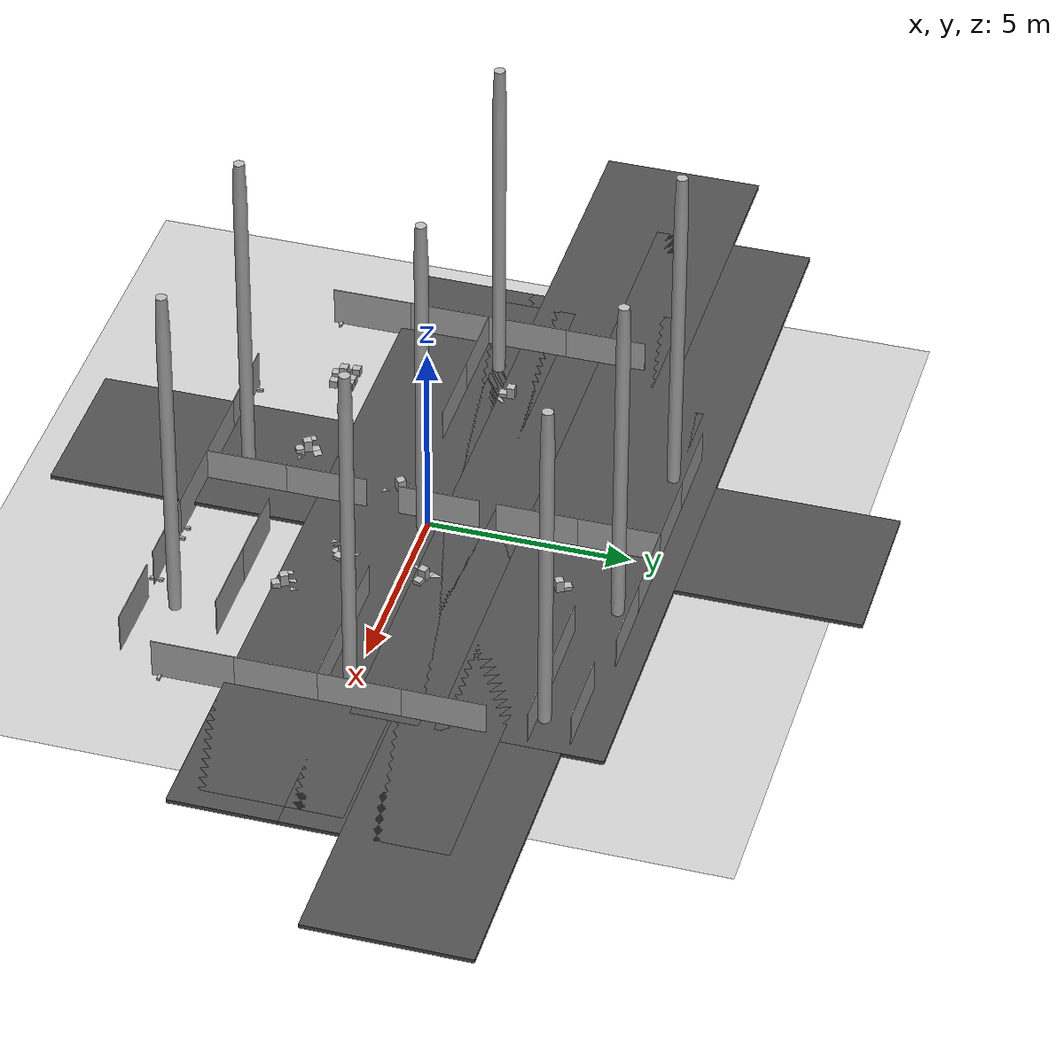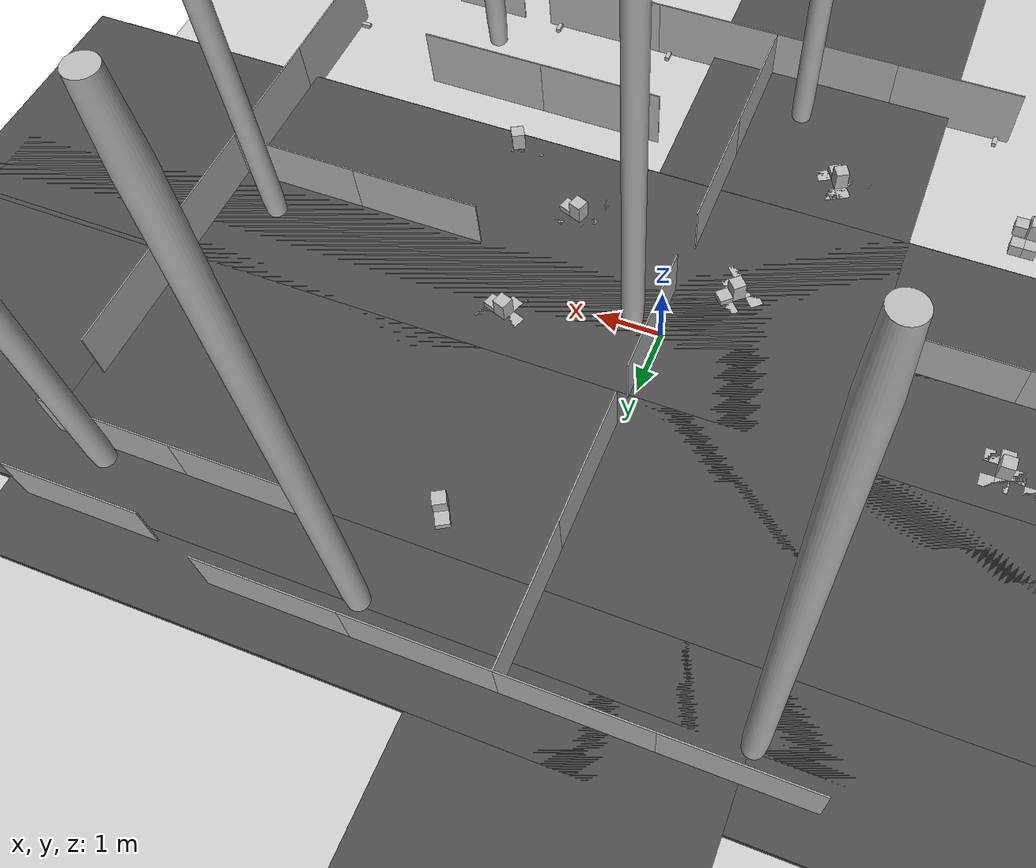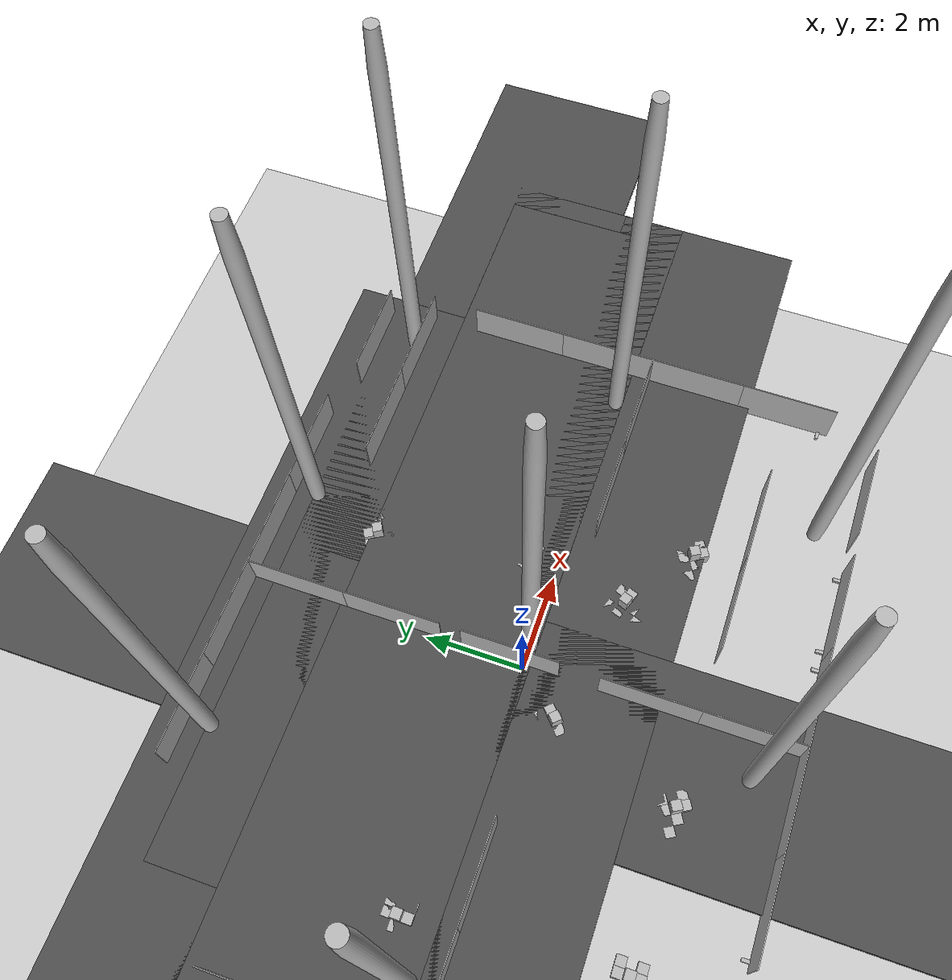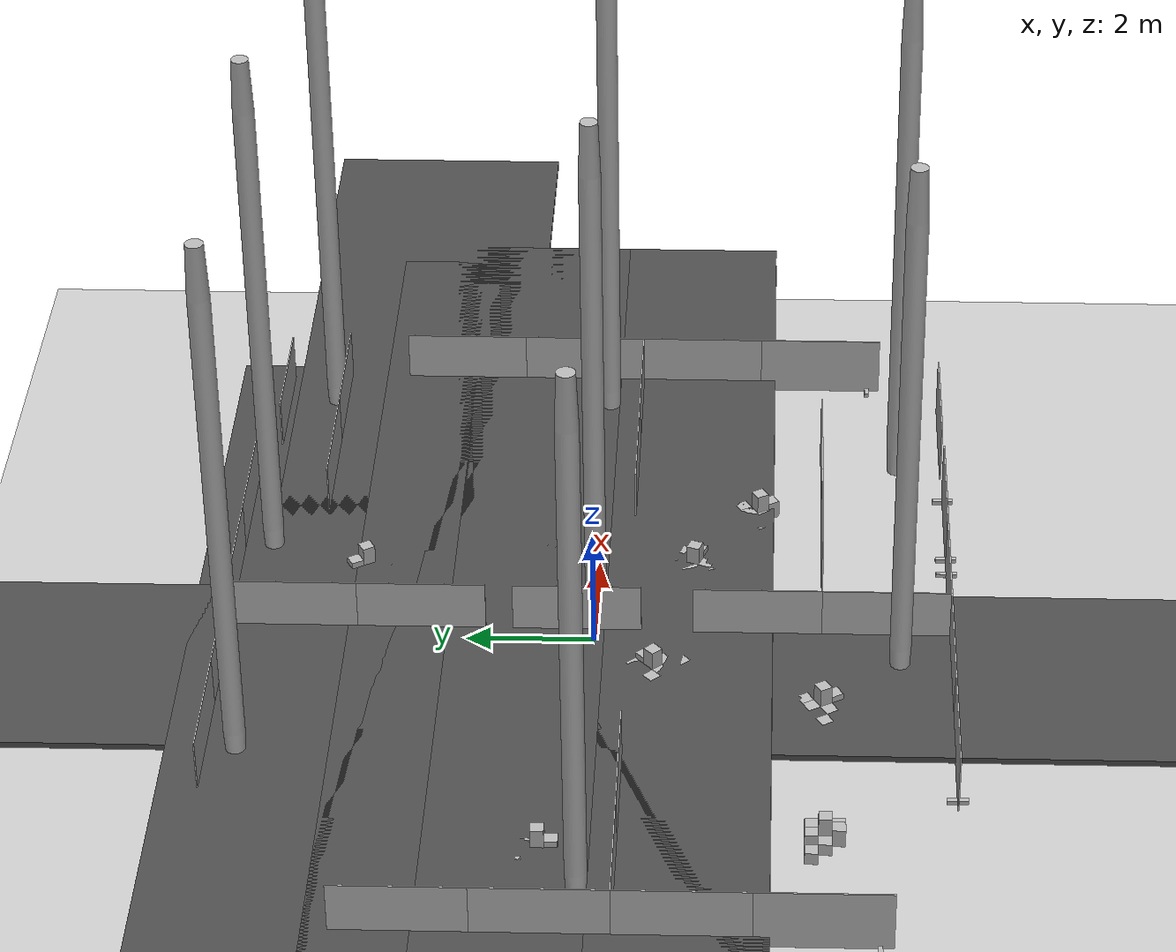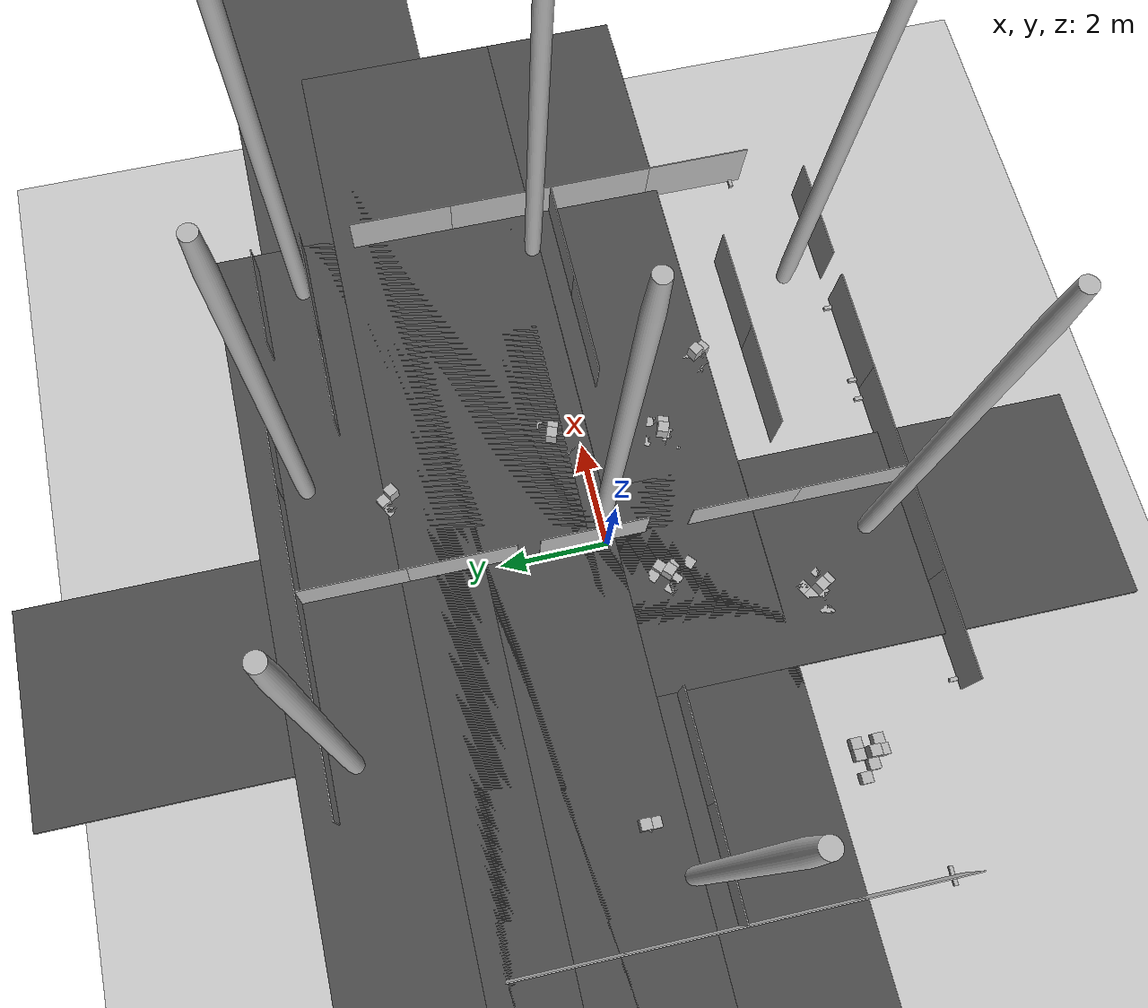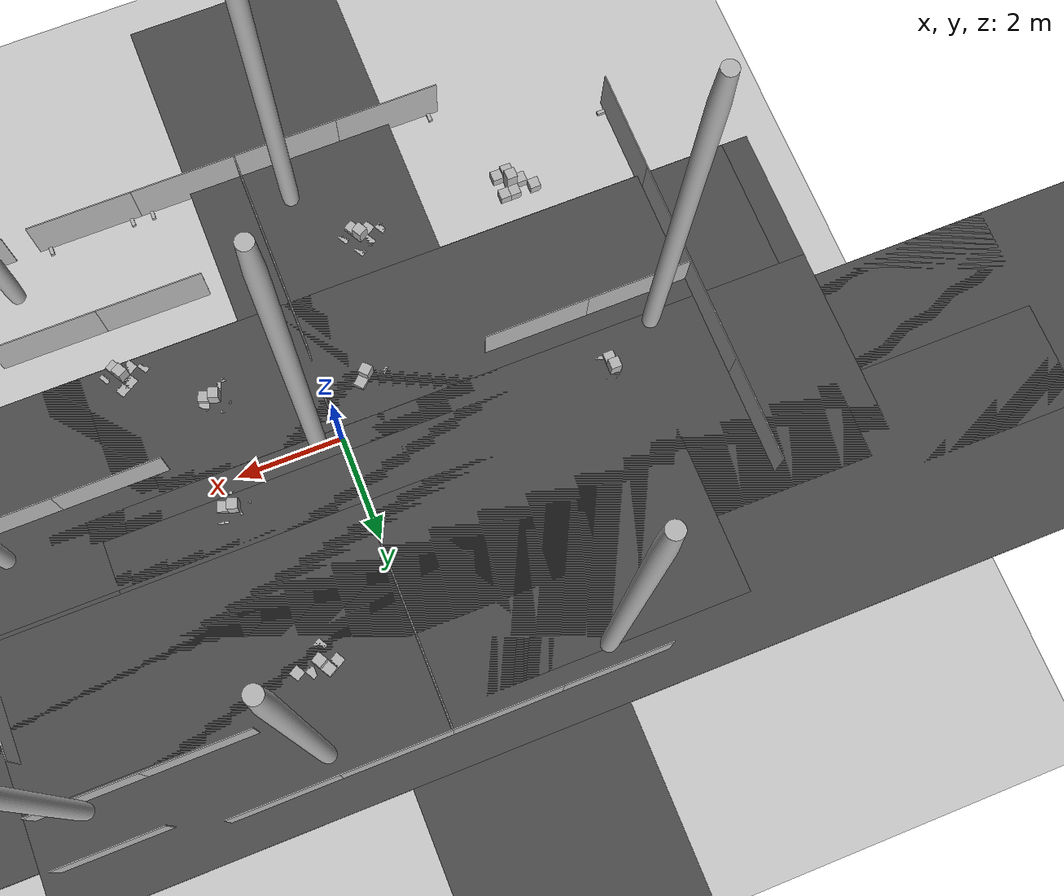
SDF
<?xml version="1.0" ?>
<sdf version="1.4">
  <!--Generated by blend2world.py-->
  <world name="default">
    <scene>
      <ambient>0.5 0.5 0.5 1</ambient>
      <background>0.5 0.5 0.5 1</background>
      <shadows>false</shadows>
    </scene>
    <plugin name="ros_interface_plugin" filename="librotors_gazebo_ros_interface_plugin.so"></plugin>
    <physics type="ode">
      <gravity>0 0 -9.81</gravity>
      <ode>
        <solver>
          <type>quick</type>
          <iters>1000</iters>
          <sor>1.3</sor>
        </solver>
        <constraints>
          <cfm>0.0</cfm>
          <erp>0.2</erp>
          <contact_max_correcting_vel>100.0</contact_max_correcting_vel>
          <contact_surface_layer>0.001</contact_surface_layer>
        </constraints>
      </ode>
      <real_time_update_rate>120</real_time_update_rate>
      <real_time_factor>1</real_time_factor>
      <max_step_size>0.008333</max_step_size>
    </physics>
    <light name="directional_light_1" type="directional">
      <cast_shadows>false</cast_shadows>
      <pose>0 0 30 0.1 0.1 0</pose>
      <diffuse>1.0 1.0 1.0 1</diffuse>
      <specular>.1 .1 .1 1</specular>
      <attenuation>
        <range>300</range>
      </attenuation>
      <direction>0.1 0.1 -1</direction>
    </light>
    <include>
      <uri>model://custom_ground_plane</uri>
    </include>
    <light name="directional_light.-10.0_-12.0" type="sun">
      <pose>-10.0 -12.0 8  0 0 0</pose>
      <cast_shadows>1</cast_shadows>
      <diffuse>0.5 0.5 0.5 1</diffuse>
      <specular>0.1 0.1 0.1 1</specular>
      <attenuation>
        <range>20</range>
        <constant>0.5</constant>
        <linear>0.01</linear>
        <quadratic>0.00</quadratic>
      </attenuation>
      <direction>0.1 0.1 -1.0</direction>
    </light>
    <light name="directional_light.-10.0_0.0" type="sun">
      <pose>-10.0 0.0 8  0 0 0</pose>
      <cast_shadows>1</cast_shadows>
      <diffuse>0.5 0.5 0.5 1</diffuse>
      <specular>0.1 0.1 0.1 1</specular>
      <attenuation>
        <range>20</range>
        <constant>0.5</constant>
        <linear>0.01</linear>
        <quadratic>0.00</quadratic>
      </attenuation>
      <direction>0.1 0.1 -1.0</direction>
    </light>
    <light name="directional_light.-10.0_12.0" type="sun">
      <pose>-10.0 12.0 8  0 0 0</pose>
      <cast_shadows>1</cast_shadows>
      <diffuse>0.5 0.5 0.5 1</diffuse>
      <specular>0.1 0.1 0.1 1</specular>
      <attenuation>
        <range>20</range>
        <constant>0.5</constant>
        <linear>0.01</linear>
        <quadratic>0.00</quadratic>
      </attenuation>
      <direction>0.1 0.1 -1.0</direction>
    </light>
    <light name="directional_light.0.0_-12.0" type="sun">
      <pose>0.0 -12.0 8  0 0 0</pose>
      <cast_shadows>1</cast_shadows>
      <diffuse>0.5 0.5 0.5 1</diffuse>
      <specular>0.1 0.1 0.1 1</specular>
      <attenuation>
        <range>20</range>
        <constant>0.5</constant>
        <linear>0.01</linear>
        <quadratic>0.00</quadratic>
      </attenuation>
      <direction>0.1 0.1 -1.0</direction>
    </light>
    <light name="directional_light.0.0_0.0" type="sun">
      <pose>0.0 0.0 8  0 0 0</pose>
      <cast_shadows>1</cast_shadows>
      <diffuse>0.5 0.5 0.5 1</diffuse>
      <specular>0.1 0.1 0.1 1</specular>
      <attenuation>
        <range>20</range>
        <constant>0.5</constant>
        <linear>0.01</linear>
        <quadratic>0.00</quadratic>
      </attenuation>
      <direction>0.1 0.1 -1.0</direction>
    </light>
    <light name="directional_light.0.0_12.0" type="sun">
      <pose>0.0 12.0 8  0 0 0</pose>
      <cast_shadows>1</cast_shadows>
      <diffuse>0.5 0.5 0.5 1</diffuse>
      <specular>0.1 0.1 0.1 1</specular>
      <attenuation>
        <range>20</range>
        <constant>0.5</constant>
        <linear>0.01</linear>
        <quadratic>0.00</quadratic>
      </attenuation>
      <direction>0.1 0.1 -1.0</direction>
    </light>
    <light name="directional_light.10.0_-12.0" type="sun">
      <pose>10.0 -12.0 8  0 0 0</pose>
      <cast_shadows>1</cast_shadows>
      <diffuse>0.5 0.5 0.5 1</diffuse>
      <specular>0.1 0.1 0.1 1</specular>
      <attenuation>
        <range>20</range>
        <constant>0.5</constant>
        <linear>0.01</linear>
        <quadratic>0.00</quadratic>
      </attenuation>
      <direction>0.1 0.1 -1.0</direction>
    </light>
    <light name="directional_light.10.0_0.0" type="sun">
      <pose>10.0 0.0 8  0 0 0</pose>
      <cast_shadows>1</cast_shadows>
      <diffuse>0.5 0.5 0.5 1</diffuse>
      <specular>0.1 0.1 0.1 1</specular>
      <attenuation>
        <range>20</range>
        <constant>0.5</constant>
        <linear>0.01</linear>
        <quadratic>0.00</quadratic>
      </attenuation>
      <direction>0.1 0.1 -1.0</direction>
    </light>
    <light name="directional_light.10.0_12.0" type="sun">
      <pose>10.0 12.0 8  0 0 0</pose>
      <cast_shadows>1</cast_shadows>
      <diffuse>0.5 0.5 0.5 1</diffuse>
      <specular>0.1 0.1 0.1 1</specular>
      <attenuation>
        <range>20</range>
        <constant>0.5</constant>
        <linear>0.01</linear>
        <quadratic>0.00</quadratic>
      </attenuation>
      <direction>0.1 0.1 -1.0</direction>
    </light>
    <include>
      <name>wall_2x1.083</name>
      <pose>-7.0 2.468942403793335 0.5130000114440918  0.0 -0.0 1.570796251296997</pose>
      <uri>model://wall_2x1</uri>
    </include>
    <include>
      <name>wall_2x1.084</name>
      <pose>-4.0 -0.531057596206665 0.5130000114440918  0.0 0.0 0.0</pose>
      <uri>model://wall_2x1</uri>
    </include>
    <include>
      <name>wall_stand.169</name>
      <pose>-1.8005000352859497 2.0 0.03449999913573265  0.0 -0.0 1.570796251296997</pose>
      <uri>model://wall_stand</uri>
    </include>
    <include>
      <name>wall_stand.170</name>
      <pose>-0.19949999451637268 2.0 0.03449999913573265  0.0 -0.0 1.570796251296997</pose>
      <uri>model://wall_stand</uri>
    </include>
    <include>
      <name>wall_2x1.085</name>
      <pose>-7.0 0.46894240379333496 0.5130000114440918  0.0 -0.0 1.570796251296997</pose>
      <uri>model://wall_2x1</uri>
    </include>
    <include>
      <name>wall_2x1.086</name>
      <pose>-7.0 -3.531057596206665 0.5130000114440918  0.0 -0.0 1.570796251296997</pose>
      <uri>model://wall_2x1</uri>
    </include>
    <include>
      <name>wall_2x1.087</name>
      <pose>-7.0 -1.531057596206665 0.5130000114440918  0.0 -0.0 1.570796251296997</pose>
      <uri>model://wall_2x1</uri>
    </include>
    <include>
      <name>wall_2x1.088</name>
      <pose>-6.0 -0.531057596206665 0.5130000114440918  0.0 0.0 0.0</pose>
      <uri>model://wall_2x1</uri>
    </include>
    <include>
      <name>wall_stand.177</name>
      <pose>-0.19949999451637268 2.0 0.03449999913573265  0.0 -0.0 1.570796251296997</pose>
      <uri>model://wall_stand</uri>
    </include>
    <include>
      <name>wall_stand.167</name>
      <pose>-7.0 3.269442558288574 0.03449999913573265  0.0 0.0 0.0</pose>
      <uri>model://wall_stand</uri>
    </include>
    <include>
      <name>wall_stand.168</name>
      <pose>-7.0 1.6684424877166748 0.03449999913573265  0.0 0.0 0.0</pose>
      <uri>model://wall_stand</uri>
    </include>
    <include>
      <name>wall_stand.171</name>
      <pose>-7.0 1.2694425582885742 0.03449999913573265  0.0 0.0 0.0</pose>
      <uri>model://wall_stand</uri>
    </include>
    <include>
      <name>wall_stand.172</name>
      <pose>-7.0 -0.3315575122833252 0.03449999913573265  0.0 0.0 0.0</pose>
      <uri>model://wall_stand</uri>
    </include>
    <include>
      <name>wall_stand.173</name>
      <pose>-7.0 -4.331557273864746 0.03449999913573265  0.0 0.0 0.0</pose>
      <uri>model://wall_stand</uri>
    </include>
    <include>
      <name>wall_stand.174</name>
      <pose>-7.0 -2.730557680130005 0.03449999913573265  0.0 0.0 0.0</pose>
      <uri>model://wall_stand</uri>
    </include>
    <include>
      <name>wall_stand.175</name>
      <pose>-7.0 -0.7305574417114258 0.03449999913573265  0.0 0.0 0.0</pose>
      <uri>model://wall_stand</uri>
    </include>
    <include>
      <name>wall_stand.176</name>
      <pose>-7.0 -2.331557512283325 0.03449999913573265  0.0 0.0 0.0</pose>
      <uri>model://wall_stand</uri>
    </include>
    <include>
      <name>cube_20x20.010</name>
      <pose>-5.073810577392578 0.8086726665496826 0.10000000149011612  0.0 -0.0 3.141592502593994</pose>
      <uri>model://cube_20x20</uri>
    </include>
    <include>
      <name>cube_20x20.011</name>
      <pose>-5.273810386657715 0.6086728572845459 0.10000000149011612  0.0 -0.0 3.141592502593994</pose>
      <uri>model://cube_20x20</uri>
    </include>
    <include>
      <name>cube_20x20.012</name>
      <pose>-5.473810195922852 0.8086726665496826 0.10000000149011612  0.0 -0.0 3.141592502593994</pose>
      <uri>model://cube_20x20</uri>
    </include>
    <include>
      <name>cube_20x20.013</name>
      <pose>-4.873810291290283 0.8086726665496826 0.10000000149011612  0.0 -0.0 3.141592502593994</pose>
      <uri>model://cube_20x20</uri>
    </include>
    <include>
      <name>cube_20x20.014</name>
      <pose>-4.873810291290283 0.4086730480194092 0.10000000149011612  0.0 -0.0 3.141592502593994</pose>
      <uri>model://cube_20x20</uri>
    </include>
    <include>
      <name>cube_20x30.002</name>
      <pose>-5.073810577392578 0.4086730480194092 0.15000000596046448  0.0 -0.0 3.141592502593994</pose>
      <uri>model://cube_20x30</uri>
    </include>
    <include>
      <name>cube_20x50.002</name>
      <pose>-5.073810577392578 0.6086728572845459 0.25  0.0 -0.0 3.141592502593994</pose>
      <uri>model://cube_20x50</uri>
    </include>
    <include>
      <name>cube_20x20.015</name>
      <pose>-5.073810577392578 0.8086726665496826 0.10000000149011612  0.0 -0.0 3.141592502593994</pose>
      <uri>model://cube_20x20</uri>
    </include>
    <include>
      <name>cube_20x20.016</name>
      <pose>-5.273810386657715 0.6086728572845459 0.10000000149011612  0.0 -0.0 3.141592502593994</pose>
      <uri>model://cube_20x20</uri>
    </include>
    <include>
      <name>cube_20x20.017</name>
      <pose>-5.473810195922852 0.8086726665496826 0.10000000149011612  0.0 -0.0 3.141592502593994</pose>
      <uri>model://cube_20x20</uri>
    </include>
    <include>
      <name>cube_20x20.018</name>
      <pose>-4.873810291290283 0.8086726665496826 0.10000000149011612  0.0 -0.0 3.141592502593994</pose>
      <uri>model://cube_20x20</uri>
    </include>
    <include>
      <name>cube_20x20.019</name>
      <pose>-4.873810291290283 0.4086730480194092 0.10000000149011612  0.0 -0.0 3.141592502593994</pose>
      <uri>model://cube_20x20</uri>
    </include>
    <include>
      <name>cube_20x30.003</name>
      <pose>-5.073810577392578 0.4086730480194092 0.15000000596046448  0.0 -0.0 3.141592502593994</pose>
      <uri>model://cube_20x30</uri>
    </include>
    <include>
      <name>cube_20x50.003</name>
      <pose>-5.073810577392578 0.6086728572845459 0.25  0.0 -0.0 3.141592502593994</pose>
      <uri>model://cube_20x50</uri>
    </include>
    <include>
      <name>ramp.008</name>
      <pose>1.2565653324127197 1.8507144451141357 0.15000000596046448  0.0 0.0 0.0</pose>
      <uri>model://ramp</uri>
    </include>
    <include>
      <name>ramp.009</name>
      <pose>0.7436184883117676 1.8457143306732178 0.15000000596046448  0.0 -0.0 3.141592502593994</pose>
      <uri>model://ramp</uri>
    </include>
    <include>
      <name>ramp.010</name>
      <pose>-0.9832800030708313 0.8252742290496826 0.15000000596046448  0.0 -0.0 7.853981971740723</pose>
      <uri>model://ramp</uri>
    </include>
    <include>
      <name>wall_2x1.097</name>
      <pose>7.071430206298828 -3.531057596206665 0.5130000114440918  0.0 -0.0 4.71238899230957</pose>
      <uri>model://wall_2x1</uri>
    </include>
    <include>
      <name>wall_2x1.098</name>
      <pose>4.071430206298828 -0.5310573577880859 0.5130000114440918  0.0 -0.0 3.141592502593994</pose>
      <uri>model://wall_2x1</uri>
    </include>
    <include>
      <name>wall_stand.191</name>
      <pose>-1.8005000352859497 2.0 0.03449999913573265  0.0 -0.0 1.570796251296997</pose>
      <uri>model://wall_stand</uri>
    </include>
    <include>
      <name>wall_stand.192</name>
      <pose>-0.19949999451637268 2.0 0.03449999913573265  0.0 -0.0 1.570796251296997</pose>
      <uri>model://wall_stand</uri>
    </include>
    <include>
      <name>wall_2x1.099</name>
      <pose>7.071430206298828 -1.531057596206665 0.5130000114440918  0.0 -0.0 4.71238899230957</pose>
      <uri>model://wall_2x1</uri>
    </include>
    <include>
      <name>wall_2x1.100</name>
      <pose>7.071430206298828 2.468942403793335 0.5130000114440918  0.0 -0.0 4.71238899230957</pose>
      <uri>model://wall_2x1</uri>
    </include>
    <include>
      <name>wall_2x1.101</name>
      <pose>7.071430206298828 0.46894240379333496 0.5130000114440918  0.0 -0.0 4.71238899230957</pose>
      <uri>model://wall_2x1</uri>
    </include>
    <include>
      <name>wall_2x1.102</name>
      <pose>6.071430206298828 -0.5310574769973755 0.5130000114440918  0.0 -0.0 3.141592502593994</pose>
      <uri>model://wall_2x1</uri>
    </include>
    <include>
      <name>wall_stand.199</name>
      <pose>-0.19949999451637268 2.0 0.03449999913573265  0.0 -0.0 1.570796251296997</pose>
      <uri>model://wall_stand</uri>
    </include>
    <include>
      <name>wall_stand.189</name>
      <pose>7.071430206298828 -4.331557273864746 0.03450000286102295  0.0 -0.0 3.141592502593994</pose>
      <uri>model://wall_stand</uri>
    </include>
    <include>
      <name>wall_stand.190</name>
      <pose>7.071430206298828 -2.730557680130005 0.03450000286102295  0.0 -0.0 3.141592502593994</pose>
      <uri>model://wall_stand</uri>
    </include>
    <include>
      <name>wall_stand.193</name>
      <pose>7.071430206298828 -2.3315577507019043 0.03450000286102295  0.0 -0.0 3.141592502593994</pose>
      <uri>model://wall_stand</uri>
    </include>
    <include>
      <name>wall_stand.194</name>
      <pose>7.071430206298828 -0.7305576801300049 0.03450000286102295  0.0 -0.0 3.141592502593994</pose>
      <uri>model://wall_stand</uri>
    </include>
    <include>
      <name>wall_stand.195</name>
      <pose>7.071430206298828 3.269442319869995 0.03450000286102295  0.0 -0.0 3.141592502593994</pose>
      <uri>model://wall_stand</uri>
    </include>
    <include>
      <name>wall_stand.196</name>
      <pose>7.071430206298828 1.6684424877166748 0.03450000286102295  0.0 -0.0 3.141592502593994</pose>
      <uri>model://wall_stand</uri>
    </include>
    <include>
      <name>wall_stand.197</name>
      <pose>7.071430206298828 -0.3315577507019043 0.03450000286102295  0.0 -0.0 3.141592502593994</pose>
      <uri>model://wall_stand</uri>
    </include>
    <include>
      <name>wall_stand.198</name>
      <pose>7.071430206298828 1.2694423198699951 0.03450000286102295  0.0 -0.0 3.141592502593994</pose>
      <uri>model://wall_stand</uri>
    </include>
    <include>
      <name>wall_2x1.103</name>
      <pose>-2.989354133605957 -5.530285835266113 0.5130000114440918  0.0 -0.0 3.141592502593994</pose>
      <uri>model://wall_2x1</uri>
    </include>
    <include>
      <name>wall_2x1.104</name>
      <pose>0.010646045207977295 -2.5302858352661133 0.5130000114440918  0.0 -0.0 1.570796251296997</pose>
      <uri>model://wall_2x1</uri>
    </include>
    <include>
      <name>wall_stand.202</name>
      <pose>-1.8005000352859497 2.0 0.03449999913573265  0.0 -0.0 1.570796251296997</pose>
      <uri>model://wall_stand</uri>
    </include>
    <include>
      <name>wall_stand.203</name>
      <pose>-0.19949999451637268 2.0 0.03449999913573265  0.0 -0.0 1.570796251296997</pose>
      <uri>model://wall_stand</uri>
    </include>
    <include>
      <name>wall_2x1.105</name>
      <pose>-0.9893541932106018 -5.530285835266113 0.5130000114440918  0.0 -0.0 3.141592502593994</pose>
      <uri>model://wall_2x1</uri>
    </include>
    <include>
      <name>wall_2x1.106</name>
      <pose>3.010645627975464 -5.530285835266113 0.5130000114440918  0.0 -0.0 3.141592502593994</pose>
      <uri>model://wall_2x1</uri>
    </include>
    <include>
      <name>wall_2x1.107</name>
      <pose>1.010645866394043 -5.530285835266113 0.5130000114440918  0.0 -0.0 3.141592502593994</pose>
      <uri>model://wall_2x1</uri>
    </include>
    <include>
      <name>wall_2x1.108</name>
      <pose>0.010645806789398193 -4.530285835266113 0.5130000114440918  0.0 -0.0 1.570796251296997</pose>
      <uri>model://wall_2x1</uri>
    </include>
    <include>
      <name>wall_stand.210</name>
      <pose>-0.19949999451637268 2.0 0.03449999913573265  0.0 -0.0 1.570796251296997</pose>
      <uri>model://wall_stand</uri>
    </include>
    <include>
      <name>wall_stand.200</name>
      <pose>-3.7898542881011963 -5.530285835266113 0.03450000286102295  0.0 -0.0 1.570796251296997</pose>
      <uri>model://wall_stand</uri>
    </include>
    <include>
      <name>wall_stand.201</name>
      <pose>-2.188854217529297 -5.530285835266113 0.03450000286102295  0.0 -0.0 1.570796251296997</pose>
      <uri>model://wall_stand</uri>
    </include>
    <include>
      <name>wall_stand.204</name>
      <pose>-1.7898542881011963 -5.530285835266113 0.03450000286102295  0.0 -0.0 1.570796251296997</pose>
      <uri>model://wall_stand</uri>
    </include>
    <include>
      <name>wall_stand.205</name>
      <pose>-0.18885427713394165 -5.530285835266113 0.03450000286102295  0.0 -0.0 1.570796251296997</pose>
      <uri>model://wall_stand</uri>
    </include>
    <include>
      <name>wall_stand.206</name>
      <pose>3.811145544052124 -5.530285835266113 0.03450000286102295  0.0 -0.0 1.570796251296997</pose>
      <uri>model://wall_stand</uri>
    </include>
    <include>
      <name>wall_stand.207</name>
      <pose>2.210145950317383 -5.530285835266113 0.03450000286102295  0.0 -0.0 1.570796251296997</pose>
      <uri>model://wall_stand</uri>
    </include>
    <include>
      <name>wall_stand.208</name>
      <pose>0.21014565229415894 -5.530285835266113 0.03450000286102295  0.0 -0.0 1.570796251296997</pose>
      <uri>model://wall_stand</uri>
    </include>
    <include>
      <name>wall_stand.209</name>
      <pose>1.8111457824707031 -5.530285835266113 0.03450000286102295  0.0 -0.0 1.570796251296997</pose>
      <uri>model://wall_stand</uri>
    </include>
    <include>
      <name>cube_20x20.020</name>
      <pose>-4.71690034866333 -3.3630831241607666 0.10000000149011612  0.0 -0.0 3.141592502593994</pose>
      <uri>model://cube_20x20</uri>
    </include>
    <include>
      <name>cube_20x20.021</name>
      <pose>-4.916900157928467 -3.5630829334259033 0.10000000149011612  0.0 -0.0 3.141592502593994</pose>
      <uri>model://cube_20x20</uri>
    </include>
    <include>
      <name>cube_20x20.022</name>
      <pose>-5.1168999671936035 -3.3630831241607666 0.10000000149011612  0.0 -0.0 3.141592502593994</pose>
      <uri>model://cube_20x20</uri>
    </include>
    <include>
      <name>cube_20x20.023</name>
      <pose>-4.516900062561035 -3.3630831241607666 0.10000000149011612  0.0 -0.0 3.141592502593994</pose>
      <uri>model://cube_20x20</uri>
    </include>
    <include>
      <name>cube_20x20.024</name>
      <pose>-4.516900062561035 -3.76308274269104 0.10000000149011612  0.0 -0.0 3.141592502593994</pose>
      <uri>model://cube_20x20</uri>
    </include>
    <include>
      <name>cube_20x20.025</name>
      <pose>-4.71690034866333 -3.3630831241607666 0.10000000149011612  0.0 -0.0 3.141592502593994</pose>
      <uri>model://cube_20x20</uri>
    </include>
    <include>
      <name>cube_20x20.026</name>
      <pose>-4.916900157928467 -3.5630829334259033 0.10000000149011612  0.0 -0.0 3.141592502593994</pose>
      <uri>model://cube_20x20</uri>
    </include>
    <include>
      <name>cube_20x20.027</name>
      <pose>-5.1168999671936035 -3.3630831241607666 0.10000000149011612  0.0 -0.0 3.141592502593994</pose>
      <uri>model://cube_20x20</uri>
    </include>
    <include>
      <name>cube_20x20.028</name>
      <pose>-4.516900062561035 -3.3630831241607666 0.10000000149011612  0.0 -0.0 3.141592502593994</pose>
      <uri>model://cube_20x20</uri>
    </include>
    <include>
      <name>cube_20x20.029</name>
      <pose>-4.516900062561035 -3.76308274269104 0.10000000149011612  0.0 -0.0 3.141592502593994</pose>
      <uri>model://cube_20x20</uri>
    </include>
    <include>
      <name>cube_20x30.004</name>
      <pose>-4.71690034866333 -3.76308274269104 0.15000000596046448  0.0 -0.0 3.141592502593994</pose>
      <uri>model://cube_20x30</uri>
    </include>
    <include>
      <name>cube_20x30.005</name>
      <pose>-4.71690034866333 -3.76308274269104 0.15000000596046448  0.0 -0.0 3.141592502593994</pose>
      <uri>model://cube_20x30</uri>
    </include>
    <include>
      <name>cube_20x50.004</name>
      <pose>-4.71690034866333 -3.5630829334259033 0.25  0.0 -0.0 3.141592502593994</pose>
      <uri>model://cube_20x50</uri>
    </include>
    <include>
      <name>cube_20x50.005</name>
      <pose>-4.71690034866333 -3.5630829334259033 0.25  0.0 -0.0 3.141592502593994</pose>
      <uri>model://cube_20x50</uri>
    </include>
    <include>
      <name>cube_20x20.030</name>
      <pose>-1.7805752754211426 -3.3717634677886963 0.10000000149011612  0.0 -0.0 3.6651763916015625</pose>
      <uri>model://cube_20x20</uri>
    </include>
    <include>
      <name>cube_20x20.031</name>
      <pose>-1.8537843227386475 -3.6449673175811768 0.10000000149011612  0.0 -0.0 3.6651763916015625</pose>
      <uri>model://cube_20x20</uri>
    </include>
    <include>
      <name>cube_20x20.032</name>
      <pose>-2.126988172531128 -3.5717580318450928 0.10000000149011612  0.0 -0.0 3.6651763916015625</pose>
      <uri>model://cube_20x20</uri>
    </include>
    <include>
      <name>cube_20x20.033</name>
      <pose>-1.6073683500289917 -3.271765947341919 0.10000000149011612  0.0 -0.0 3.6651763916015625</pose>
      <uri>model://cube_20x20</uri>
    </include>
    <include>
      <name>cube_20x20.034</name>
      <pose>-1.4073739051818848 -3.6181790828704834 0.10000000149011612  0.0 -0.0 3.6651763916015625</pose>
      <uri>model://cube_20x20</uri>
    </include>
    <include>
      <name>cube_20x20.035</name>
      <pose>-1.7805752754211426 -3.3717634677886963 0.10000000149011612  0.0 -0.0 3.6651763916015625</pose>
      <uri>model://cube_20x20</uri>
    </include>
    <include>
      <name>cube_20x20.036</name>
      <pose>-1.8537843227386475 -3.6449673175811768 0.10000000149011612  0.0 -0.0 3.6651763916015625</pose>
      <uri>model://cube_20x20</uri>
    </include>
    <include>
      <name>cube_20x20.037</name>
      <pose>-2.126988172531128 -3.5717580318450928 0.10000000149011612  0.0 -0.0 3.6651763916015625</pose>
      <uri>model://cube_20x20</uri>
    </include>
    <include>
      <name>cube_20x20.038</name>
      <pose>-1.6073683500289917 -3.271765947341919 0.10000000149011612  0.0 -0.0 3.6651763916015625</pose>
      <uri>model://cube_20x20</uri>
    </include>
    <include>
      <name>cube_20x20.039</name>
      <pose>-1.4073739051818848 -3.6181790828704834 0.10000000149011612  0.0 -0.0 3.6651763916015625</pose>
      <uri>model://cube_20x20</uri>
    </include>
    <include>
      <name>cube_20x30.006</name>
      <pose>-1.580580711364746 -3.7181766033172607 0.15000000596046448  0.0 -0.0 3.6651763916015625</pose>
      <uri>model://cube_20x30</uri>
    </include>
    <include>
      <name>cube_20x30.007</name>
      <pose>-1.580580711364746 -3.7181766033172607 0.15000000596046448  0.0 -0.0 3.6651763916015625</pose>
      <uri>model://cube_20x30</uri>
    </include>
    <include>
      <name>cube_20x50.006</name>
      <pose>-1.6805779933929443 -3.5449702739715576 0.25  0.0 -0.0 3.6651763916015625</pose>
      <uri>model://cube_20x50</uri>
    </include>
    <include>
      <name>cube_20x50.007</name>
      <pose>-1.6805779933929443 -3.5449702739715576 0.25  0.0 -0.0 3.6651763916015625</pose>
      <uri>model://cube_20x50</uri>
    </include>
    <include>
      <name>cube_20x20.050</name>
      <pose>2.0343916416168213 0.613365888595581 0.10000000149011612  0.0 0.0 4.376082897186279</pose>
      <uri>model://cube_20x20</uri>
    </include>
    <include>
      <name>cube_20x20.051</name>
      <pose>2.1571874618530273 0.358569860458374 0.10000000149011612  0.0 0.0 4.376082897186279</pose>
      <uri>model://cube_20x20</uri>
    </include>
    <include>
      <name>cube_20x20.052</name>
      <pose>1.902390956878662 0.23577475547790527 0.10000000149011612  0.0 0.0 4.376082897186279</pose>
      <uri>model://cube_20x20</uri>
    </include>
    <include>
      <name>cube_20x20.053</name>
      <pose>2.1003925800323486 0.8021619319915771 0.10000000149011612  0.0 0.0 4.376082897186279</pose>
      <uri>model://cube_20x20</uri>
    </include>
    <include>
      <name>cube_20x20.054</name>
      <pose>2.4779841899871826 0.6701610088348389 0.10000000149011612  0.0 0.0 4.376082897186279</pose>
      <uri>model://cube_20x20</uri>
    </include>
    <include>
      <name>cube_20x20.055</name>
      <pose>2.0343916416168213 0.613365888595581 0.10000000149011612  0.0 0.0 4.376082897186279</pose>
      <uri>model://cube_20x20</uri>
    </include>
    <include>
      <name>cube_20x20.056</name>
      <pose>2.1571874618530273 0.358569860458374 0.10000000149011612  0.0 0.0 4.376082897186279</pose>
      <uri>model://cube_20x20</uri>
    </include>
    <include>
      <name>cube_20x20.057</name>
      <pose>1.902390956878662 0.23577475547790527 0.10000000149011612  0.0 0.0 4.376082897186279</pose>
      <uri>model://cube_20x20</uri>
    </include>
    <include>
      <name>cube_20x20.058</name>
      <pose>2.1003925800323486 0.8021619319915771 0.10000000149011612  0.0 0.0 4.376082897186279</pose>
      <uri>model://cube_20x20</uri>
    </include>
    <include>
      <name>cube_20x20.059</name>
      <pose>2.4779841899871826 0.6701610088348389 0.10000000149011612  0.0 0.0 4.376082897186279</pose>
      <uri>model://cube_20x20</uri>
    </include>
    <include>
      <name>cube_20x30.010</name>
      <pose>2.4119834899902344 0.4813649654388428 0.15000000596046448  0.0 0.0 4.376082897186279</pose>
      <uri>model://cube_20x30</uri>
    </include>
    <include>
      <name>cube_20x30.011</name>
      <pose>2.4119834899902344 0.4813649654388428 0.15000000596046448  0.0 0.0 4.376082897186279</pose>
      <uri>model://cube_20x30</uri>
    </include>
    <include>
      <name>cube_20x50.010</name>
      <pose>2.2231879234313965 0.5473649501800537 0.25  0.0 0.0 4.376082897186279</pose>
      <uri>model://cube_20x50</uri>
    </include>
    <include>
      <name>cube_20x50.011</name>
      <pose>2.2231879234313965 0.5473649501800537 0.25  0.0 0.0 4.376082897186279</pose>
      <uri>model://cube_20x50</uri>
    </include>
    <include>
      <name>ramp.011</name>
      <pose>1.2565653324127197 -0.7687876224517822 0.15000000596046448  0.0 0.0 0.0</pose>
      <uri>model://ramp</uri>
    </include>
    <include>
      <name>ramp.012</name>
      <pose>0.7436184883117676 -0.7737877368927002 0.15000000596046448  0.0 -0.0 3.141592502593994</pose>
      <uri>model://ramp</uri>
    </include>
    <include>
      <name>cube_20x20.060</name>
      <pose>-0.978894829750061 -1.071094274520874 0.10000000149011612  0.0 0.0 5.4528021812438965</pose>
      <uri>model://cube_20x20</uri>
    </include>
    <include>
      <name>cube_20x20.061</name>
      <pose>-0.6963385343551636 -1.0838134288787842 0.10000000149011612  0.0 0.0 5.4528021812438965</pose>
      <uri>model://cube_20x20</uri>
    </include>
    <include>
      <name>cube_20x20.062</name>
      <pose>-0.709058403968811 -1.3663697242736816 0.10000000149011612  0.0 0.0 5.4528021812438965</pose>
      <uri>model://cube_20x20</uri>
    </include>
    <include>
      <name>cube_20x20.063</name>
      <pose>-1.1138131618499756 -0.9234559535980225 0.10000000149011612  0.0 0.0 5.4528021812438965</pose>
      <uri>model://cube_20x20</uri>
    </include>
    <include>
      <name>cube_20x20.064</name>
      <pose>-0.8185372948646545 -0.6536192893981934 0.10000000149011612  0.0 0.0 5.4528021812438965</pose>
      <uri>model://cube_20x20</uri>
    </include>
    <include>
      <name>cube_20x20.065</name>
      <pose>-0.978894829750061 -1.071094274520874 0.10000000149011612  0.0 0.0 5.4528021812438965</pose>
      <uri>model://cube_20x20</uri>
    </include>
    <include>
      <name>cube_20x20.066</name>
      <pose>-0.6963385343551636 -1.0838134288787842 0.10000000149011612  0.0 0.0 5.4528021812438965</pose>
      <uri>model://cube_20x20</uri>
    </include>
    <include>
      <name>cube_20x20.067</name>
      <pose>-0.709058403968811 -1.3663697242736816 0.10000000149011612  0.0 0.0 5.4528021812438965</pose>
      <uri>model://cube_20x20</uri>
    </include>
    <include>
      <name>cube_20x20.068</name>
      <pose>-1.1138131618499756 -0.9234559535980225 0.10000000149011612  0.0 0.0 5.4528021812438965</pose>
      <uri>model://cube_20x20</uri>
    </include>
    <include>
      <name>cube_20x20.069</name>
      <pose>-0.8185372948646545 -0.6536192893981934 0.10000000149011612  0.0 0.0 5.4528021812438965</pose>
      <uri>model://cube_20x20</uri>
    </include>
    <include>
      <name>cube_20x30.012</name>
      <pose>-0.6836188435554504 -0.8012573719024658 0.15000000596046448  0.0 0.0 5.4528021812438965</pose>
      <uri>model://cube_20x30</uri>
    </include>
    <include>
      <name>cube_20x30.013</name>
      <pose>-0.6836188435554504 -0.8012573719024658 0.15000000596046448  0.0 0.0 5.4528021812438965</pose>
      <uri>model://cube_20x30</uri>
    </include>
    <include>
      <name>cube_20x50.012</name>
      <pose>-0.8312562108039856 -0.9361758232116699 0.25  0.0 0.0 5.4528021812438965</pose>
      <uri>model://cube_20x50</uri>
    </include>
    <include>
      <name>cube_20x50.013</name>
      <pose>-0.8312562108039856 -0.9361758232116699 0.25  0.0 0.0 5.4528021812438965</pose>
      <uri>model://cube_20x50</uri>
    </include>
    <include>
      <name>cube_20x20.070</name>
      <pose>1.8325855731964111 3.536480188369751 0.10000000149011612  0.0 0.0 6.806769371032715</pose>
      <uri>model://cube_20x20</uri>
    </include>
    <include>
      <name>cube_20x20.071</name>
      <pose>1.905794620513916 3.8096840381622314 0.10000000149011612  0.0 0.0 6.806769371032715</pose>
      <uri>model://cube_20x20</uri>
    </include>
    <include>
      <name>cube_20x20.072</name>
      <pose>2.1789984703063965 3.7364747524261475 0.10000000149011612  0.0 0.0 6.806769371032715</pose>
      <uri>model://cube_20x20</uri>
    </include>
    <include>
      <name>cube_20x20.073</name>
      <pose>1.6593786478042603 3.4364826679229736 0.10000000149011612  0.0 0.0 6.806769371032715</pose>
      <uri>model://cube_20x20</uri>
    </include>
    <include>
      <name>cube_20x20.074</name>
      <pose>1.4593842029571533 3.782895803451538 0.10000000149011612  0.0 0.0 6.806769371032715</pose>
      <uri>model://cube_20x20</uri>
    </include>
    <include>
      <name>cube_20x20.075</name>
      <pose>1.8325855731964111 3.536480188369751 0.10000000149011612  0.0 0.0 6.806769371032715</pose>
      <uri>model://cube_20x20</uri>
    </include>
    <include>
      <name>cube_20x20.076</name>
      <pose>1.905794620513916 3.8096840381622314 0.10000000149011612  0.0 0.0 6.806769371032715</pose>
      <uri>model://cube_20x20</uri>
    </include>
    <include>
      <name>cube_20x20.077</name>
      <pose>2.1789984703063965 3.7364747524261475 0.10000000149011612  0.0 0.0 6.806769371032715</pose>
      <uri>model://cube_20x20</uri>
    </include>
    <include>
      <name>cube_20x20.078</name>
      <pose>1.6593786478042603 3.4364826679229736 0.10000000149011612  0.0 0.0 6.806769371032715</pose>
      <uri>model://cube_20x20</uri>
    </include>
    <include>
      <name>cube_20x20.079</name>
      <pose>1.4593842029571533 3.782895803451538 0.10000000149011612  0.0 0.0 6.806769371032715</pose>
      <uri>model://cube_20x20</uri>
    </include>
    <include>
      <name>cube_20x30.014</name>
      <pose>1.6325910091400146 3.8828933238983154 0.15000000596046448  0.0 0.0 6.806769371032715</pose>
      <uri>model://cube_20x30</uri>
    </include>
    <include>
      <name>cube_20x30.015</name>
      <pose>1.6325910091400146 3.8828933238983154 0.15000000596046448  0.0 0.0 6.806769371032715</pose>
      <uri>model://cube_20x30</uri>
    </include>
    <include>
      <name>cube_20x50.014</name>
      <pose>1.732588291168213 3.7096869945526123 0.25  0.0 0.0 6.806769371032715</pose>
      <uri>model://cube_20x50</uri>
    </include>
    <include>
      <name>cube_20x50.015</name>
      <pose>1.732588291168213 3.7096869945526123 0.25  0.0 0.0 6.806769371032715</pose>
      <uri>model://cube_20x50</uri>
    </include>
    <include>
      <name>wall_2x1.109</name>
      <pose>3.0413644313812256 5.695001602172852 0.5130000114440918  0.0 -0.0 6.283185005187988</pose>
      <uri>model://wall_2x1</uri>
    </include>
    <include>
      <name>wall_2x1.110</name>
      <pose>0.04136395454406738 2.695002794265747 0.5130000114440918  0.0 -0.0 4.71238899230957</pose>
      <uri>model://wall_2x1</uri>
    </include>
    <include>
      <name>wall_stand.213</name>
      <pose>-1.8005000352859497 2.0 0.03449999913573265  0.0 -0.0 1.570796251296997</pose>
      <uri>model://wall_stand</uri>
    </include>
    <include>
      <name>wall_stand.214</name>
      <pose>-0.19949999451637268 2.0 0.03449999913573265  0.0 -0.0 1.570796251296997</pose>
      <uri>model://wall_stand</uri>
    </include>
    <include>
      <name>wall_2x1.111</name>
      <pose>1.0413646697998047 5.695002555847168 0.5130000114440918  0.0 -0.0 6.283185005187988</pose>
      <uri>model://wall_2x1</uri>
    </include>
    <include>
      <name>wall_2x1.112</name>
      <pose>-2.9586355686187744 5.695002555847168 0.5130000114440918  0.0 -0.0 6.283185005187988</pose>
      <uri>model://wall_2x1</uri>
    </include>
    <include>
      <name>wall_2x1.113</name>
      <pose>-0.9586355686187744 5.695002555847168 0.5130000114440918  0.0 -0.0 6.283185005187988</pose>
      <uri>model://wall_2x1</uri>
    </include>
    <include>
      <name>wall_2x1.114</name>
      <pose>0.041364431381225586 4.695002555847168 0.5130000114440918  0.0 -0.0 4.71238899230957</pose>
      <uri>model://wall_2x1</uri>
    </include>
    <include>
      <name>wall_stand.221</name>
      <pose>-0.19949999451637268 2.0 0.03449999913573265  0.0 -0.0 1.570796251296997</pose>
      <uri>model://wall_stand</uri>
    </include>
    <include>
      <name>wall_stand.211</name>
      <pose>3.841865062713623 5.695001602172852 0.03450000286102295  0.0 -0.0 4.71238899230957</pose>
      <uri>model://wall_stand</uri>
    </include>
    <include>
      <name>wall_stand.212</name>
      <pose>2.2408647537231445 5.695002555847168 0.03450000286102295  0.0 -0.0 4.71238899230957</pose>
      <uri>model://wall_stand</uri>
    </include>
    <include>
      <name>wall_stand.215</name>
      <pose>1.8418647050857544 5.695002555847168 0.03450000286102295  0.0 -0.0 4.71238899230957</pose>
      <uri>model://wall_stand</uri>
    </include>
    <include>
      <name>wall_stand.216</name>
      <pose>0.24086451530456543 5.695002555847168 0.03450000286102295  0.0 -0.0 4.71238899230957</pose>
      <uri>model://wall_stand</uri>
    </include>
    <include>
      <name>wall_stand.217</name>
      <pose>-3.7591354846954346 5.695002555847168 0.03450000286102295  0.0 -0.0 4.71238899230957</pose>
      <uri>model://wall_stand</uri>
    </include>
    <include>
      <name>wall_stand.218</name>
      <pose>-2.1581356525421143 5.695002555847168 0.03450000286102295  0.0 -0.0 4.71238899230957</pose>
      <uri>model://wall_stand</uri>
    </include>
    <include>
      <name>wall_stand.219</name>
      <pose>-0.15813517570495605 5.695002555847168 0.03450000286102295  0.0 -0.0 4.71238899230957</pose>
      <uri>model://wall_stand</uri>
    </include>
    <include>
      <name>wall_stand.220</name>
      <pose>-1.7591354846954346 5.695002555847168 0.03450000286102295  0.0 -0.0 4.71238899230957</pose>
      <uri>model://wall_stand</uri>
    </include>
    <include>
      <name>wall_2x1.115</name>
      <pose>0.04136395454406738 0.2739219665527344 0.5130000114440918  0.0 -0.0 4.71238899230957</pose>
      <uri>model://wall_2x1</uri>
    </include>
    <include>
      <name>wall_stand.222</name>
      <pose>-1.8005000352859497 2.0 0.03449999913573265  0.0 -0.0 1.570796251296997</pose>
      <uri>model://wall_stand</uri>
    </include>
    <include>
      <name>wall_stand.223</name>
      <pose>-0.19949999451637268 2.0 0.03449999913573265  0.0 -0.0 1.570796251296997</pose>
      <uri>model://wall_stand</uri>
    </include>
    <include>
      <name>wall_2x1.116</name>
      <pose>5.476836204528809 -5.509757041931152 0.5130000114440918  0.0 -0.0 6.2831854820251465</pose>
      <uri>model://wall_2x1</uri>
    </include>
    <include>
      <name>wall_stand.224</name>
      <pose>-1.8005000352859497 2.0 0.03449999913573265  0.0 -0.0 1.570796251296997</pose>
      <uri>model://wall_stand</uri>
    </include>
    <include>
      <name>wall_stand.225</name>
      <pose>-0.19949999451637268 2.0 0.03449999913573265  0.0 -0.0 1.570796251296997</pose>
      <uri>model://wall_stand</uri>
    </include>
    <include>
      <name>wall_2x1.117</name>
      <pose>4.3128767013549805 -3.5467369556427 0.5130000114440918  0.0 -0.0 6.2831854820251465</pose>
      <uri>model://wall_2x1</uri>
    </include>
    <include>
      <name>wall_stand.226</name>
      <pose>-1.8005000352859497 2.0 0.03449999913573265  0.0 -0.0 1.570796251296997</pose>
      <uri>model://wall_stand</uri>
    </include>
    <include>
      <name>wall_stand.227</name>
      <pose>-0.19949999451637268 2.0 0.03449999913573265  0.0 -0.0 1.570796251296997</pose>
      <uri>model://wall_stand</uri>
    </include>
    <include>
      <name>wall_2x1.118</name>
      <pose>2.3128767013549805 -3.5467369556427 0.5130000114440918  0.0 -0.0 6.2831854820251465</pose>
      <uri>model://wall_2x1</uri>
    </include>
    <include>
      <name>wall_stand.228</name>
      <pose>-1.8005000352859497 2.0 0.03449999913573265  0.0 -0.0 1.570796251296997</pose>
      <uri>model://wall_stand</uri>
    </include>
    <include>
      <name>wall_stand.229</name>
      <pose>-0.19949999451637268 2.0 0.03449999913573265  0.0 -0.0 1.570796251296997</pose>
      <uri>model://wall_stand</uri>
    </include>
    <include>
      <name>ramp.013</name>
      <pose>-5.403332710266113 2.3036534786224365 0.15000000596046448  0.0 -0.0 6.283185005187988</pose>
      <uri>model://ramp</uri>
    </include>
    <include>
      <name>wall_2x1.119</name>
      <pose>5.946268081665039 5.418047904968262 0.5130000114440918  0.0 -0.0 9.42477798461914</pose>
      <uri>model://wall_2x1</uri>
    </include>
    <include>
      <name>wall_stand.230</name>
      <pose>-1.8005000352859497 2.0 0.03449999913573265  0.0 -0.0 1.570796251296997</pose>
      <uri>model://wall_stand</uri>
    </include>
    <include>
      <name>wall_stand.231</name>
      <pose>-0.19949999451637268 2.0 0.03449999913573265  0.0 -0.0 1.570796251296997</pose>
      <uri>model://wall_stand</uri>
    </include>
    <include>
      <name>wall_2x1.120</name>
      <pose>4.110227108001709 4.4550275802612305 0.5130000114440918  0.0 -0.0 9.42477798461914</pose>
      <uri>model://wall_2x1</uri>
    </include>
    <include>
      <name>wall_stand.232</name>
      <pose>-1.8005000352859497 2.0 0.03449999913573265  0.0 -0.0 1.570796251296997</pose>
      <uri>model://wall_stand</uri>
    </include>
    <include>
      <name>wall_stand.233</name>
      <pose>-0.19949999451637268 2.0 0.03449999913573265  0.0 -0.0 1.570796251296997</pose>
      <uri>model://wall_stand</uri>
    </include>
    <include>
      <name>wall_2x1.121</name>
      <pose>6.110227108001709 4.4550275802612305 0.5130000114440918  0.0 -0.0 9.42477798461914</pose>
      <uri>model://wall_2x1</uri>
    </include>
    <include>
      <name>wall_stand.234</name>
      <pose>-1.8005000352859497 2.0 0.03449999913573265  0.0 -0.0 1.570796251296997</pose>
      <uri>model://wall_stand</uri>
    </include>
    <include>
      <name>wall_stand.235</name>
      <pose>-0.19949999451637268 2.0 0.03449999913573265  0.0 -0.0 1.570796251296997</pose>
      <uri>model://wall_stand</uri>
    </include>
    <include>
      <name>ramp.014</name>
      <pose>-2.6988332271575928 2.3036534786224365 0.15000000596046448  0.0 -0.0 6.283185005187988</pose>
      <uri>model://ramp</uri>
    </include>
    <include>
      <name>ramp.015</name>
      <pose>-2.6988332271575928 4.303653717041016 0.15000000596046448  0.0 -0.0 6.283185005187988</pose>
      <uri>model://ramp</uri>
    </include>
    <include>
      <name>cube_20x20.090</name>
      <pose>3.2194247245788574 -2.3717634677886963 0.10000000149011612  0.0 -0.0 3.6651763916015625</pose>
      <uri>model://cube_20x20</uri>
    </include>
    <include>
      <name>cube_20x20.091</name>
      <pose>3.1462156772613525 -2.6449673175811768 0.10000000149011612  0.0 -0.0 3.6651763916015625</pose>
      <uri>model://cube_20x20</uri>
    </include>
    <include>
      <name>cube_20x20.092</name>
      <pose>2.873011827468872 -2.5717580318450928 0.10000000149011612  0.0 -0.0 3.6651763916015625</pose>
      <uri>model://cube_20x20</uri>
    </include>
    <include>
      <name>cube_20x20.093</name>
      <pose>3.3926315307617188 -2.271765947341919 0.10000000149011612  0.0 -0.0 3.6651763916015625</pose>
      <uri>model://cube_20x20</uri>
    </include>
    <include>
      <name>cube_20x20.094</name>
      <pose>3.5926260948181152 -2.6181790828704834 0.10000000149011612  0.0 -0.0 3.6651763916015625</pose>
      <uri>model://cube_20x20</uri>
    </include>
    <include>
      <name>cube_20x20.095</name>
      <pose>3.2194247245788574 -2.3717634677886963 0.10000000149011612  0.0 -0.0 3.6651763916015625</pose>
      <uri>model://cube_20x20</uri>
    </include>
    <include>
      <name>cube_20x20.096</name>
      <pose>3.1462156772613525 -2.6449673175811768 0.10000000149011612  0.0 -0.0 3.6651763916015625</pose>
      <uri>model://cube_20x20</uri>
    </include>
    <include>
      <name>cube_20x20.097</name>
      <pose>2.873011827468872 -2.5717580318450928 0.10000000149011612  0.0 -0.0 3.6651763916015625</pose>
      <uri>model://cube_20x20</uri>
    </include>
    <include>
      <name>cube_20x20.098</name>
      <pose>3.3926315307617188 -2.271765947341919 0.10000000149011612  0.0 -0.0 3.6651763916015625</pose>
      <uri>model://cube_20x20</uri>
    </include>
    <include>
      <name>cube_20x20.099</name>
      <pose>3.5926260948181152 -2.6181790828704834 0.10000000149011612  0.0 -0.0 3.6651763916015625</pose>
      <uri>model://cube_20x20</uri>
    </include>
    <include>
      <name>cube_20x20.100</name>
      <pose>1.691523790359497 -1.4547417163848877 0.10000000149011612  0.0 0.0 4.376082897186279</pose>
      <uri>model://cube_20x20</uri>
    </include>
    <include>
      <name>cube_20x20.101</name>
      <pose>1.8143196105957031 -1.7095377445220947 0.10000000149011612  0.0 0.0 4.376082897186279</pose>
      <uri>model://cube_20x20</uri>
    </include>
    <include>
      <name>cube_20x20.102</name>
      <pose>1.559523105621338 -1.8323333263397217 0.10000000149011612  0.0 0.0 4.376082897186279</pose>
      <uri>model://cube_20x20</uri>
    </include>
    <include>
      <name>cube_20x20.103</name>
      <pose>1.7575247287750244 -1.2659454345703125 0.10000000149011612  0.0 0.0 4.376082897186279</pose>
      <uri>model://cube_20x20</uri>
    </include>
    <include>
      <name>cube_20x20.104</name>
      <pose>2.1351163387298584 -1.3979465961456299 0.10000000149011612  0.0 0.0 4.376082897186279</pose>
      <uri>model://cube_20x20</uri>
    </include>
    <include>
      <name>cube_20x20.105</name>
      <pose>1.691523790359497 -1.4547417163848877 0.10000000149011612  0.0 0.0 4.376082897186279</pose>
      <uri>model://cube_20x20</uri>
    </include>
    <include>
      <name>cube_20x20.106</name>
      <pose>1.8143196105957031 -1.7095377445220947 0.10000000149011612  0.0 0.0 4.376082897186279</pose>
      <uri>model://cube_20x20</uri>
    </include>
    <include>
      <name>cube_20x20.107</name>
      <pose>1.559523105621338 -1.8323333263397217 0.10000000149011612  0.0 0.0 4.376082897186279</pose>
      <uri>model://cube_20x20</uri>
    </include>
    <include>
      <name>cube_20x20.108</name>
      <pose>1.7575247287750244 -1.2659454345703125 0.10000000149011612  0.0 0.0 4.376082897186279</pose>
      <uri>model://cube_20x20</uri>
    </include>
    <include>
      <name>cube_20x20.109</name>
      <pose>2.1351163387298584 -1.3979465961456299 0.10000000149011612  0.0 0.0 4.376082897186279</pose>
      <uri>model://cube_20x20</uri>
    </include>
    <include>
      <name>cube_20x30.018</name>
      <pose>3.419419288635254 -2.7181766033172607 0.15000000596046448  0.0 -0.0 3.6651763916015625</pose>
      <uri>model://cube_20x30</uri>
    </include>
    <include>
      <name>cube_20x30.019</name>
      <pose>3.419419288635254 -2.7181766033172607 0.15000000596046448  0.0 -0.0 3.6651763916015625</pose>
      <uri>model://cube_20x30</uri>
    </include>
    <include>
      <name>cube_20x30.020</name>
      <pose>2.06911563873291 -1.5867431163787842 0.15000000596046448  0.0 0.0 4.376082897186279</pose>
      <uri>model://cube_20x30</uri>
    </include>
    <include>
      <name>cube_20x30.021</name>
      <pose>2.06911563873291 -1.5867431163787842 0.15000000596046448  0.0 0.0 4.376082897186279</pose>
      <uri>model://cube_20x30</uri>
    </include>
    <include>
      <name>cube_20x50.018</name>
      <pose>3.3194220066070557 -2.5449702739715576 0.25  0.0 -0.0 3.6651763916015625</pose>
      <uri>model://cube_20x50</uri>
    </include>
    <include>
      <name>cube_20x50.019</name>
      <pose>3.3194220066070557 -2.5449702739715576 0.25  0.0 -0.0 3.6651763916015625</pose>
      <uri>model://cube_20x50</uri>
    </include>
    <include>
      <name>cube_20x50.020</name>
      <pose>1.8803200721740723 -1.520742416381836 0.25  0.0 0.0 4.376082897186279</pose>
      <uri>model://cube_20x50</uri>
    </include>
    <include>
      <name>cube_20x50.021</name>
      <pose>1.8803200721740723 -1.520742416381836 0.25  0.0 0.0 4.376082897186279</pose>
      <uri>model://cube_20x50</uri>
    </include>
    <include>
      <name>ramp.016</name>
      <pose>4.30116605758667 3.3036534786224365 0.15000000596046448  0.0 -0.0 6.283185005187988</pose>
      <uri>model://ramp</uri>
    </include>
    <include>
      <name>barrel_110l</name>
      <pose>-6.063030242919922 0.0 0.0  0.0 0.0 0.0</pose>
      <uri>model://barrel_110l</uri>
    </include>
    <include>
      <name>barrel_110l.001</name>
      <pose>-3.0217368602752686 5.237995624542236 0.0  0.0 0.0 0.0</pose>
      <uri>model://barrel_110l</uri>
    </include>
    <include>
      <name>barrel_110l.002</name>
      <pose>2.1513140201568604 5.237995624542236 0.0  0.0 0.0 0.0</pose>
      <uri>model://barrel_110l</uri>
    </include>
    <include>
      <name>barrel_110l.003</name>
      <pose>6.276121139526367 4.623660087585449 0.0  0.0 0.0 0.0</pose>
      <uri>model://barrel_110l</uri>
    </include>
    <include>
      <name>barrel_110l.004</name>
      <pose>4.665648460388184 -4.783429145812988 0.0  0.0 0.0 0.0</pose>
      <uri>model://barrel_110l</uri>
    </include>
    <include>
      <name>barrel_110l.006</name>
      <pose>6.263016223907471 -0.004051387310028076 0.0  0.0 0.0 0.0</pose>
      <uri>model://barrel_110l</uri>
    </include>
    <include>
      <name>barrel_110l.007</name>
      <pose>0.43812131881713867 -0.004051387310028076 0.0  0.0 0.0 0.0</pose>
      <uri>model://barrel_110l</uri>
    </include>
    <include>
      <name>barrel_110l.008</name>
      <pose>-0.7261247634887695 -4.73142147064209 0.0  0.0 0.0 0.0</pose>
      <uri>model://barrel_110l</uri>
    </include>
  </world>
</sdf>

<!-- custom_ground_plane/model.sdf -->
<sdf version="1.5">
  <model name="custom_ground_plane">
    <static>true</static>
    <link name="link">
      <collision name="collision">
        <geometry>
          <plane>
            <normal>0 0 1</normal>
            <size>20 20</size>
          </plane>
        </geometry>
        <surface>
          <friction>
            <ode>
              <mu>100</mu>
              <mu2>50</mu2>
            </ode>
          </friction>
        </surface>
      </collision>
      <visual name="visual">
        <cast_shadows>false</cast_shadows>
        <geometry>
          <plane>
            <normal>0 0 1</normal>
            <size>20 20</size>
          </plane>
        </geometry>
        <material>Gazebo/Gray</material>
      </visual>
    </link>
  </model>
</sdf>

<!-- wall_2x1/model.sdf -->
<sdf version="1.4">
  <!--Generated by blend2world.py-->
    <model name="wall_2x1">
      <pose>0.0 0.0 0.0  0.0 0.0 0.0</pose>
      <static>true</static>
      <link name="body">
        <collision name="collision">
          <geometry>
            <mesh>
              <uri>model://wall_2x1/meshes/wall_2x1.dae</uri>
              <scale>1 1 1</scale>
            </mesh>
          </geometry>
        </collision>
        <visual name="visual">
          <geometry>
            <mesh>
              <uri>model://wall_2x1/meshes/wall_2x1.dae</uri>
              <scale>1 1 1</scale>
            </mesh>
          </geometry>
	  <material>
            <script>
              <uri>model://wall_2x1/textures/chipboard.jpg</uri>
            </script>
          </material>
        </visual>
      </link>
    </model>
</sdf>

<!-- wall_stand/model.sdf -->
<sdf version="1.4">
  <!--Generated by blend2world.py-->
    <model name="wall_stand">
      <pose>0.0 0.0 0.0  0.0 0.0 0.0</pose>
      <static>true</static>
      <link name="body">
        <collision name="collision">
          <geometry>
            <mesh>
              <uri>model://wall_stand/meshes/wall_stand.dae</uri>
              <scale>1 1 1</scale>
            </mesh>
          </geometry>
        </collision>
        <visual name="visual">
          <geometry>
            <mesh>
              <uri>model://wall_stand/meshes/wall_stand.dae</uri>
              <scale>1 1 1</scale>
            </mesh>
          </geometry>
	  <material>
            <script>
              <uri>model://wall_stand/textures/ahorn_gr.jpg</uri>
            </script>
          </material>
        </visual>
      </link>
    </model>
</sdf>

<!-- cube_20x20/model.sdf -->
<sdf version="1.4">
  <!--Generated by blend2world.py-->
    <model name="cube_20x20">
      <pose>0.0 0.0 0.0  0.0 0.0 0.0</pose>
      <static>true</static>
      <link name="body">
        <collision name="collision">
          <geometry>
            <mesh>
              <uri>model://cube_20x20/meshes/cube_20x20.dae</uri>
              <scale>1 1 1</scale>
            </mesh>
          </geometry>
        </collision>
        <visual name="visual">
          <geometry>
            <mesh>
              <uri>model://cube_20x20/meshes/cube_20x20.dae</uri>
              <scale>1 1 1</scale>
            </mesh>
          </geometry>
	  <material>
            <script>
              <uri>model://cube_20x20/textures/chipboard.jpg</uri>
            </script>
          </material>
        </visual>
      </link>
    </model>
</sdf>

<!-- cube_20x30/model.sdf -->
<sdf version="1.4">
  <!--Generated by blend2world.py-->
    <model name="cube_20x30">
      <pose>0.0 0.0 0.0  0.0 0.0 0.0</pose>
      <static>true</static>
      <link name="body">
        <collision name="collision">
          <geometry>
            <mesh>
              <uri>model://cube_20x30/meshes/cube_20x30.dae</uri>
              <scale>1 1 1</scale>
            </mesh>
          </geometry>
        </collision>
        <visual name="visual">
          <geometry>
            <mesh>
              <uri>model://cube_20x30/meshes/cube_20x30.dae</uri>
              <scale>1 1 1</scale>
            </mesh>
          </geometry>
	  <material>
            <script>
              <uri>model://cube_20x30/textures/chipboard.jpg</uri>
            </script>
          </material>
        </visual>
      </link>
    </model>
</sdf>

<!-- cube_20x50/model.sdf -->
<sdf version="1.4">
  <!--Generated by blend2world.py-->
    <model name="cube_20x50">
      <pose>0.0 0.0 0.0  0.0 0.0 0.0</pose>
      <static>true</static>
      <link name="body">
        <collision name="collision">
          <geometry>
            <mesh>
              <uri>model://cube_20x50/meshes/cube_20x50.dae</uri>
              <scale>1 1 1</scale>
            </mesh>
          </geometry>
        </collision>
        <visual name="visual">
          <geometry>
            <mesh>
              <uri>model://cube_20x50/meshes/cube_20x50.dae</uri>
              <scale>1 1 1</scale>
            </mesh>
          </geometry>
	  <material>
            <script>
              <uri>model://cube_20x50/textures/chipboard.jpg</uri>
            </script>
          </material>
        </visual>
      </link>
    </model>
</sdf>

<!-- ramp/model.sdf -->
<sdf version="1.4">
  <model name="ramp">
    <static>true</static>
    <pose>0 0 0.2 0 0.15 0</pose>
    <link name="link">
      <collision name="collision">
        <geometry>
          <box>
            <size>20 4 .1</size>
          </box>
        </geometry>
      </collision>
      <visual name="visual">
        <geometry>
          <box>
            <size>20 4 .1</size>
          </box>
        </geometry>
        <material>
          <script>
            <uri>model://asphalt_plane/materials/scripts/asphalt.material</uri>
            <name>vrc/asphalt</name>
          </script>
        </material>
      </visual>
    </link>
  </model>
</sdf>

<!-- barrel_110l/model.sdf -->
<sdf version="1.4">
  <!--Generated by blend2world.py-->
    <model name="barel_110l">
      <pose>0.0 0.0 0.0  0.0 0.0 0.0</pose>
      <static>true</static>
      <link name="body">
        <collision name="collision">
          <geometry>
            <mesh>
              <uri>model://barrel_110l/meshes/barrel_110l.dae</uri>
              <scale>1 1 15</scale>
            </mesh>
          </geometry>
        </collision>
        <visual name="visual">
          <geometry>
            <mesh>
              <uri>model://barrel_110l/meshes/barrel_110l.dae</uri>
              <scale>1 1 15</scale>
            </mesh>
          </geometry>
	  <material>
            <script>
              <uri>model://barrel_110l/textures/barrel_110l.jpg</uri>
            </script>
          </material>
        </visual>
      </link>
    </model>
</sdf>
